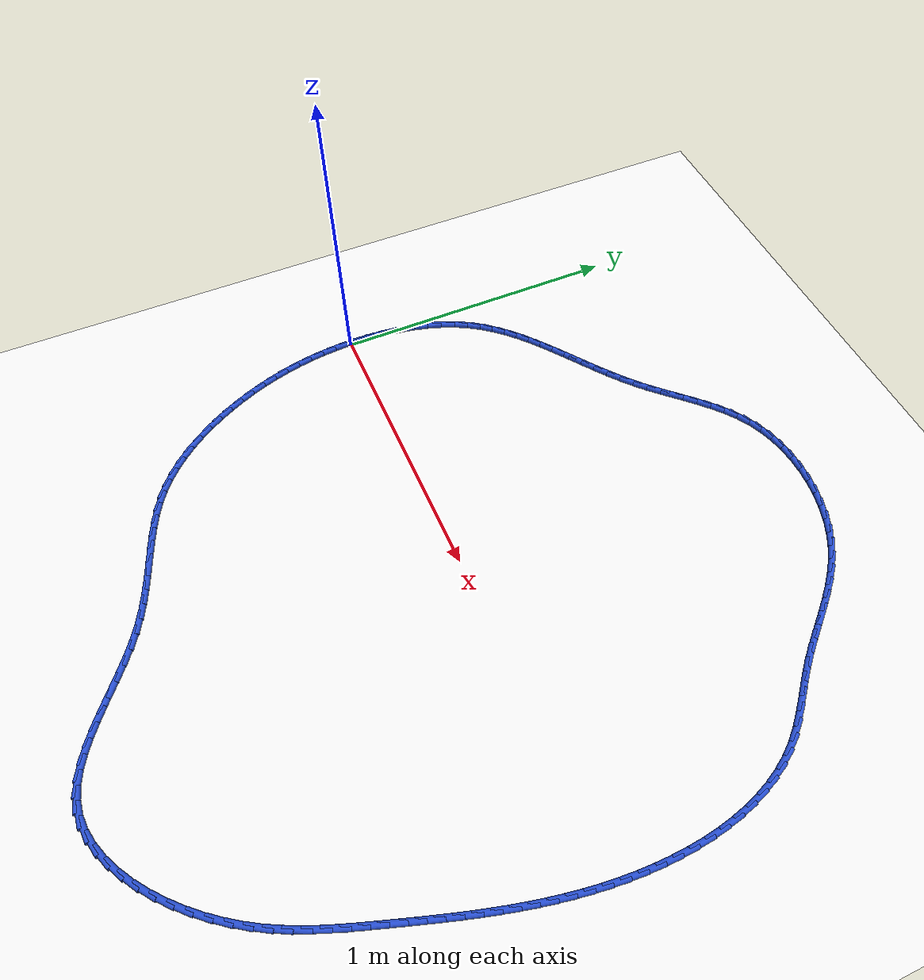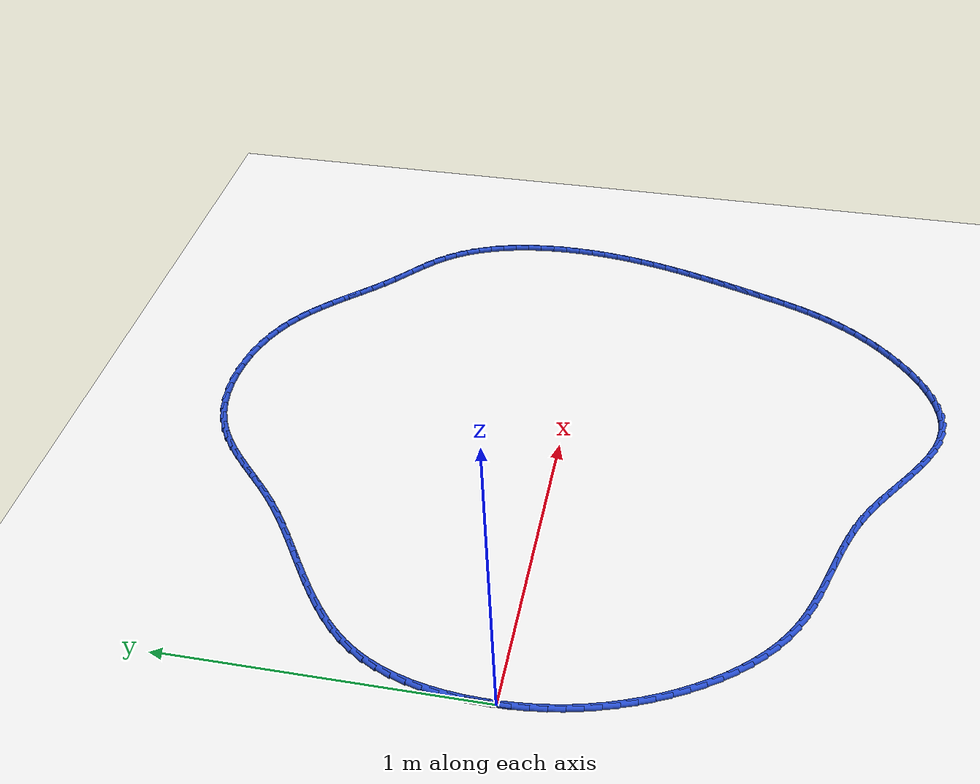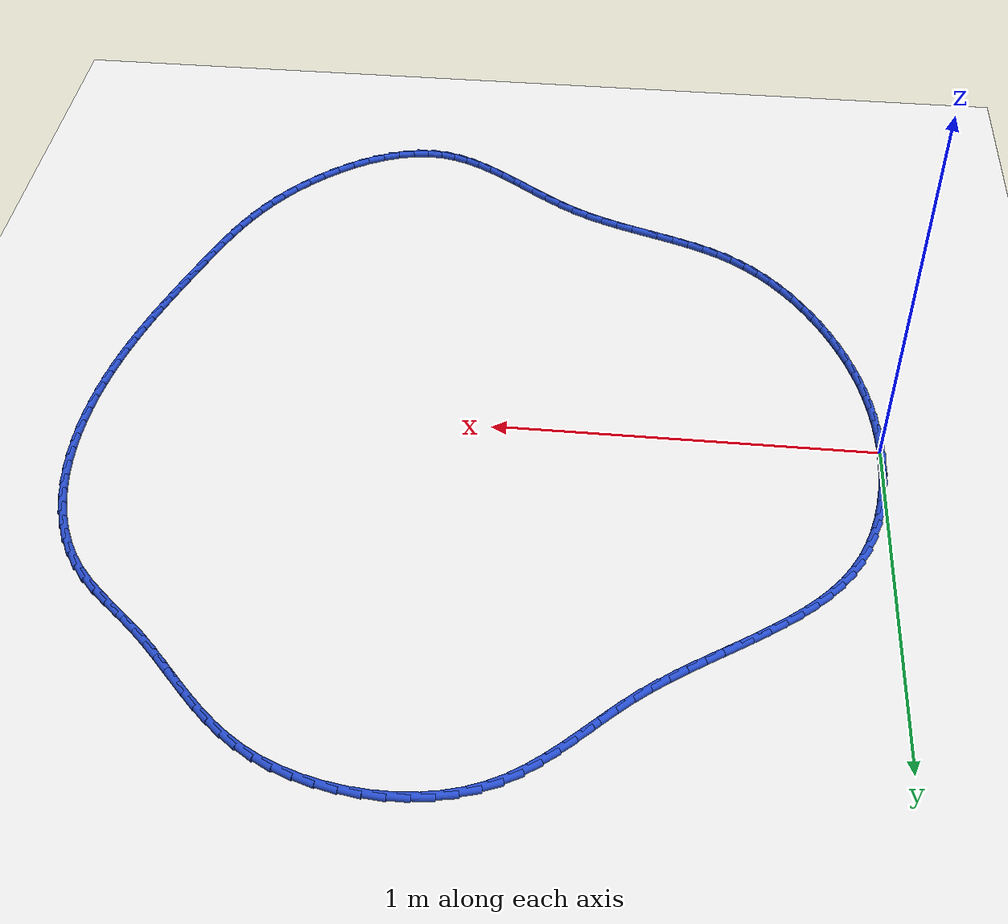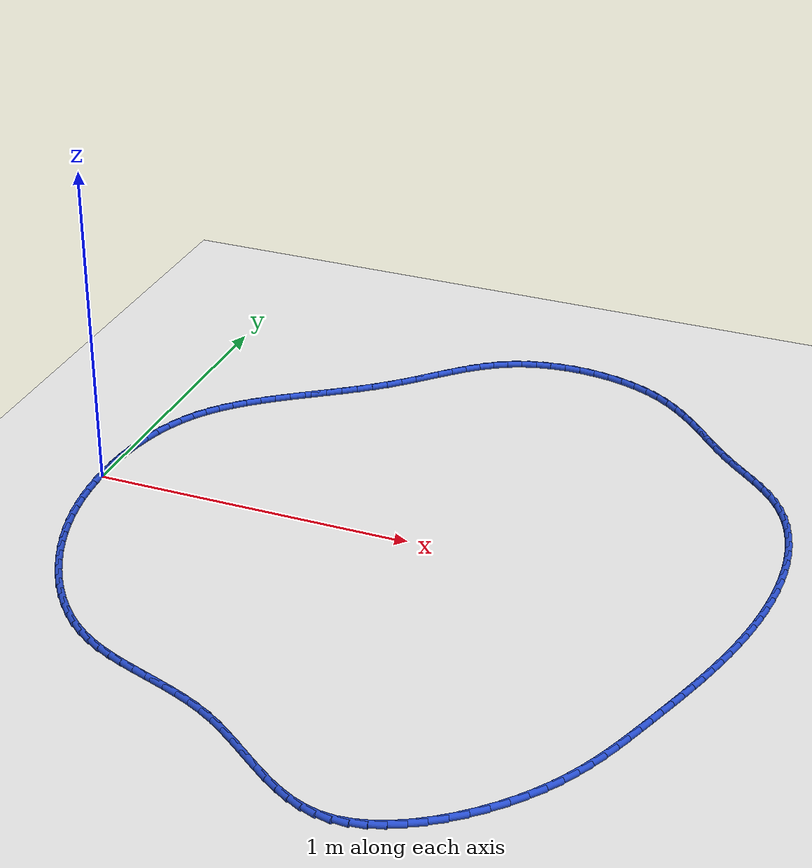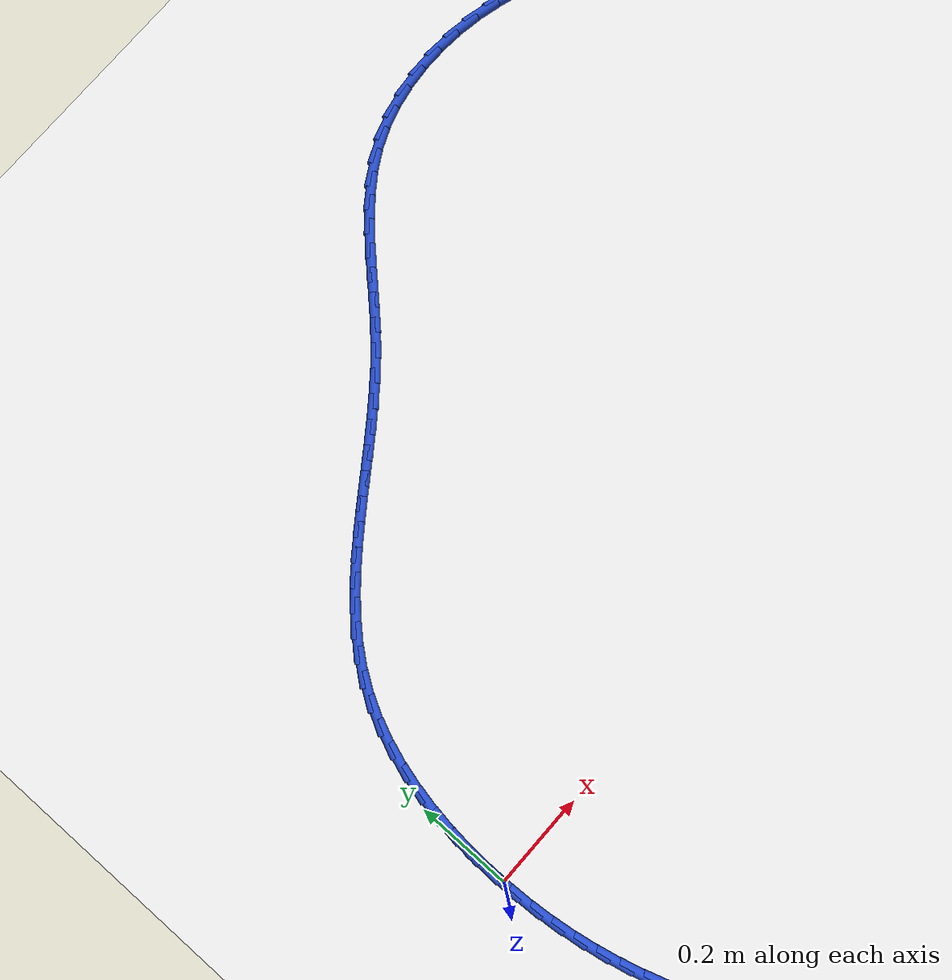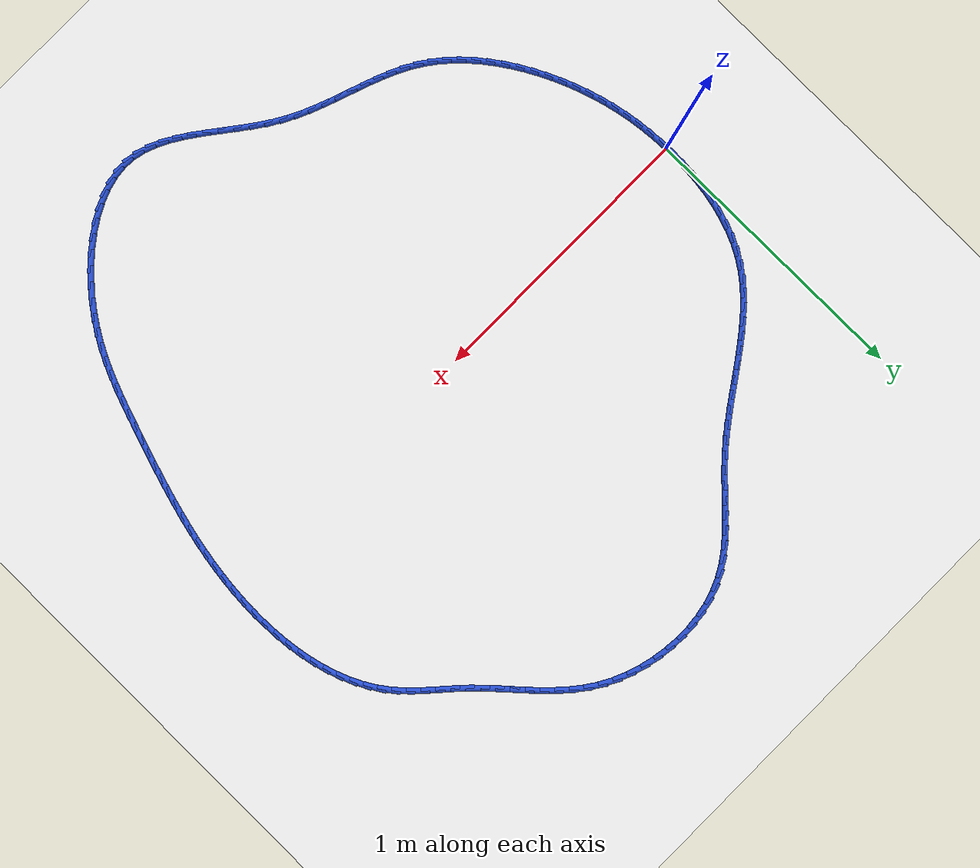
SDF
<sdf version="1.6">
 <world name="default">
  <light name="sun" type="directional">
   <pose>0 0 10 0 -0 0</pose>
   <diffuse>0.8 0.8 0.8 1</diffuse>
   <specular>0.2 0.2 0.2 1</specular>
   <attenuation>
    <range>1000</range>
    <constant>0.9</constant>
    <linear>0.01</linear>
    <quadratic>0.001</quadratic>
   </attenuation>
   <direction>-0.5 0.1 -0.9</direction>
  </light>
  <model name="ground_plane">
   <static>1</static>
   <link name="link">
    <collision name="collision">
     <geometry><plane><normal>0 0 1</normal><size>100 100</size></plane></geometry>
     <surface><friction><ode><mu>100</mu><mu2>50</mu2></ode></friction></surface>
    </collision>
    <visual name="visual">
     <cast_shadows>0</cast_shadows>
     <geometry><plane><normal>0 0 1</normal><size>100 100</size></plane></geometry>
     <material>
      <script><uri>file://media/materials/scripts/gazebo.material</uri><name>Gazebo/WhiteGlow</name></script>
     </material>
    </visual>
   </link>
  </model>
  <gravity>0 0 -9.8</gravity>
  <magnetic_field>6e-06 2.3e-05 -4.2e-05</magnetic_field>
  <atmosphere type="adiabatic"/>
  <physics name="default_physics" default="0" type="ode">
   <max_step_size>0.001</max_step_size>
   <real_time_factor>1</real_time_factor>
   <real_time_update_rate>1000</real_time_update_rate>
  </physics>
  <scene><ambient>0.4 0.4 0.4 1</ambient><background>0.7 0.7 0.7 1</background><shadows>1</shadows></scene>
  <spherical_coordinates>
   <surface_model>EARTH_WGS84</surface_model>
   <latitude_deg>0</latitude_deg>
   <longitude_deg>0</longitude_deg>
   <elevation>0</elevation>
   <heading_deg>0</heading_deg>
  </spherical_coordinates>
  <model name="line">
   <link name="link_0">
    <pose>1.3877787807814457e-17 1.6653345369377348e-16 0.01 0 1.57 1.5703879840936825</pose>
    <collision name="collision">
     <geometry><cylinder><radius>0.01</radius><length>0.08</length></cylinder></geometry>
    </collision>
    <visual name="visual">
     <material>
      <script><name>Gazebo/Blue</name><uri>file://media/materials/scripts/gazebo.material</uri></script>
     </material>
     <geometry><cylinder><radius>0.01</radius><length>0.08</length></cylinder></geometry>
    </visual>
   </link>
   <link name="link_1">
    <pose>2.0461932362918987e-05 0.05010970237685566 0.01 0 1.57 1.5252319487551422</pose>
    <collision name="collision">
     <geometry><cylinder><radius>0.01</radius><length>0.08</length></cylinder></geometry>
    </collision>
    <visual name="visual">
     <material>
      <script><name>Gazebo/Blue</name><uri>file://media/materials/scripts/gazebo.material</uri></script>
     </material>
     <geometry><cylinder><radius>0.01</radius><length>0.08</length></cylinder></geometry>
    </visual>
   </link>
   <link name="link_2">
    <pose>0.002315027762263988 0.10043361292031516 0.01 0 1.57 1.4768614780469314</pose>
    <collision name="collision">
     <geometry><cylinder><radius>0.01</radius><length>0.08</length></cylinder></geometry>
    </collision>
    <visual name="visual">
     <material>
      <script><name>Gazebo/Blue</name><uri>file://media/materials/scripts/gazebo.material</uri></script>
     </material>
     <geometry><cylinder><radius>0.01</radius><length>0.08</length></cylinder></geometry>
    </visual>
   </link>
   <link name="link_3">
    <pose>0.007041752678469361 0.15060470815478336 0.01 0 1.57 1.4244827749581548</pose>
    <collision name="collision">
     <geometry><cylinder><radius>0.01</radius><length>0.08</length></cylinder></geometry>
    </collision>
    <visual name="visual">
     <material>
      <script><name>Gazebo/Blue</name><uri>file://media/materials/scripts/gazebo.material</uri></script>
     </material>
     <geometry><cylinder><radius>0.01</radius><length>0.08</length></cylinder></geometry>
    </visual>
   </link>
   <link name="link_4">
    <pose>0.014358691869745163 0.20025596460466466 0.01 0 1.57 1.3672498876681252</pose>
    <collision name="collision">
     <geometry><cylinder><radius>0.01</radius><length>0.08</length></cylinder></geometry>
    </collision>
    <visual name="visual">
     <material>
      <script><name>Gazebo/Blue</name><uri>file://media/materials/scripts/gazebo.material</uri></script>
     </material>
     <geometry><cylinder><radius>0.01</radius><length>0.08</length></cylinder></geometry>
    </visual>
   </link>
   <link name="link_5">
    <pose>0.02442390052485755 0.2490203587943638 0.01 0 1.57 1.3042676388788637</pose>
    <collision name="collision">
     <geometry><cylinder><radius>0.01</radius><length>0.08</length></cylinder></geometry>
    </collision>
    <visual name="visual">
     <material>
      <script><name>Gazebo/Blue</name><uri>file://media/materials/scripts/gazebo.material</uri></script>
     </material>
     <geometry><cylinder><radius>0.01</radius><length>0.08</length></cylinder></geometry>
    </visual>
   </link>
   <link name="link_6">
    <pose>0.03739543383257267 0.2965308672482853 0.01 0 1.57 1.2346155950224973</pose>
    <collision name="collision">
     <geometry><cylinder><radius>0.01</radius><length>0.08</length></cylinder></geometry>
    </collision>
    <visual name="visual">
     <material>
      <script><name>Gazebo/Blue</name><uri>file://media/materials/scripts/gazebo.material</uri></script>
     </material>
     <geometry><cylinder><radius>0.01</radius><length>0.08</length></cylinder></geometry>
    </visual>
   </link>
   <link name="link_7">
    <pose>0.05343134698165662 0.34242046649083346 0.01 0 1.57 1.1574041959296875</pose>
    <collision name="collision">
     <geometry><cylinder><radius>0.01</radius><length>0.08</length></cylinder></geometry>
    </collision>
    <visual name="visual">
     <material>
      <script><name>Gazebo/Blue</name><uri>file://media/materials/scripts/gazebo.material</uri></script>
     </material>
     <geometry><cylinder><radius>0.01</radius><length>0.08</length></cylinder></geometry>
    </visual>
   </link>
   <link name="link_8">
    <pose>0.0726896951608756 0.3863221330464132 0.01 0 1.57 1.0718764269249268</pose>
    <collision name="collision">
     <geometry><cylinder><radius>0.01</radius><length>0.08</length></cylinder></geometry>
    </collision>
    <visual name="visual">
     <material>
      <script><name>Gazebo/Blue</name><uri>file://media/materials/scripts/gazebo.material</uri></script>
     </material>
     <geometry><cylinder><radius>0.01</radius><length>0.08</length></cylinder></geometry>
    </visual>
   </link>
   <link name="link_9">
    <pose>0.09532853355899572 0.42786884343942905 0.01 0 1.57 0.9794280090093584</pose>
    <collision name="collision">
     <geometry><cylinder><radius>0.01</radius><length>0.08</length></cylinder></geometry>
    </collision>
    <visual name="visual">
     <material>
      <script><name>Gazebo/Blue</name><uri>file://media/materials/scripts/gazebo.material</uri></script>
     </material>
     <geometry><cylinder><radius>0.01</radius><length>0.08</length></cylinder></geometry>
    </visual>
   </link>
   <link name="link_10">
    <pose>0.12144964194261251 0.46676621261109913 0.01 0 1.57 0.8923825192492111</pose>
    <collision name="collision">
     <geometry><cylinder><radius>0.01</radius><length>0.08</length></cylinder></geometry>
    </collision>
    <visual name="visual">
     <material>
      <script><name>Gazebo/Blue</name><uri>file://media/materials/scripts/gazebo.material</uri></script>
     </material>
     <geometry><cylinder><radius>0.01</radius><length>0.08</length></cylinder></geometry>
    </visual>
   </link>
   <link name="link_11">
    <pose>0.15079946091751076 0.5031785153061151 0.01 0 1.57 0.8167372482739383</pose>
    <collision name="collision">
     <geometry><cylinder><radius>0.01</radius><length>0.08</length></cylinder></geometry>
    </collision>
    <visual name="visual">
     <material>
      <script><name>Gazebo/Blue</name><uri>file://media/materials/scripts/gazebo.material</uri></script>
     </material>
     <geometry><cylinder><radius>0.01</radius><length>0.08</length></cylinder></geometry>
    </visual>
   </link>
   <link name="link_12">
    <pose>0.1829861221882732 0.5374485507337933 0.01 0 1.57 0.7532143176928595</pose>
    <collision name="collision">
     <geometry><cylinder><radius>0.01</radius><length>0.08</length></cylinder></geometry>
    </collision>
    <visual name="visual">
     <material>
      <script><name>Gazebo/Blue</name><uri>file://media/materials/scripts/gazebo.material</uri></script>
     </material>
     <geometry><cylinder><radius>0.01</radius><length>0.08</length></cylinder></geometry>
    </visual>
   </link>
   <link name="link_13">
    <pose>0.21761744660018034 0.5699195193501528 0.01 0 1.57 0.7018589598342855</pose>
    <collision name="collision">
     <geometry><cylinder><radius>0.01</radius><length>0.08</length></cylinder></geometry>
    </collision>
    <visual name="visual">
     <material>
      <script><name>Gazebo/Blue</name><uri>file://media/materials/scripts/gazebo.material</uri></script>
     </material>
     <geometry><cylinder><radius>0.01</radius><length>0.08</length></cylinder></geometry>
    </visual>
   </link>
   <link name="link_14">
    <pose>0.2543012549985125 0.6009346216112119 0.01 0 1.57 0.6623294533921383</pose>
    <collision name="collision">
     <geometry><cylinder><radius>0.01</radius><length>0.08</length></cylinder></geometry>
    </collision>
    <visual name="visual">
     <material>
      <script><name>Gazebo/Blue</name><uri>file://media/materials/scripts/gazebo.material</uri></script>
     </material>
     <geometry><cylinder><radius>0.01</radius><length>0.08</length></cylinder></geometry>
    </visual>
   </link>
   <link name="link_15">
    <pose>0.2926453682285506 0.6308370579729903 0.01 0 1.57 0.6341263456896873</pose>
    <collision name="collision">
     <geometry><cylinder><radius>0.01</radius><length>0.08</length></cylinder></geometry>
    </collision>
    <visual name="visual">
     <material>
      <script><name>Gazebo/Blue</name><uri>file://media/materials/scripts/gazebo.material</uri></script>
     </material>
     <geometry><cylinder><radius>0.01</radius><length>0.08</length></cylinder></geometry>
    </visual>
   </link>
   <link name="link_16">
    <pose>0.33225760713557484 0.659970028891506 0.01 0 1.57 0.6167503019242502</pose>
    <collision name="collision">
     <geometry><cylinder><radius>0.01</radius><length>0.08</length></cylinder></geometry>
    </collision>
    <visual name="visual">
     <material>
      <script><name>Gazebo/Blue</name><uri>file://media/materials/scripts/gazebo.material</uri></script>
     </material>
     <geometry><cylinder><radius>0.01</radius><length>0.08</length></cylinder></geometry>
    </visual>
   </link>
   <link name="link_17">
    <pose>0.37274579256486573 0.6886767348227782 0.01 0 1.57 0.6097961670701354</pose>
    <collision name="collision">
     <geometry><cylinder><radius>0.01</radius><length>0.08</length></cylinder></geometry>
    </collision>
    <visual name="visual">
     <material>
      <script><name>Gazebo/Blue</name><uri>file://media/materials/scripts/gazebo.material</uri></script>
     </material>
     <geometry><cylinder><radius>0.01</radius><length>0.08</length></cylinder></geometry>
    </visual>
   </link>
   <link name="link_18">
    <pose>0.4137177453617037 0.7173003762228252 0.01 0 1.57 0.6129990291934921</pose>
    <collision name="collision">
     <geometry><cylinder><radius>0.01</radius><length>0.08</length></cylinder></geometry>
    </collision>
    <visual name="visual">
     <material>
      <script><name>Gazebo/Blue</name><uri>file://media/materials/scripts/gazebo.material</uri></script>
     </material>
     <geometry><cylinder><radius>0.01</radius><length>0.08</length></cylinder></geometry>
    </visual>
   </link>
   <link name="link_19">
    <pose>0.4547812863713694 0.7461841535476663 0.01 0 1.57 0.626245689992034</pose>
    <collision name="collision">
     <geometry><cylinder><radius>0.01</radius><length>0.08</length></cylinder></geometry>
    </collision>
    <visual name="visual">
     <material>
      <script><name>Gazebo/Blue</name><uri>file://media/materials/scripts/gazebo.material</uri></script>
     </material>
     <geometry><cylinder><radius>0.01</radius><length>0.08</length></cylinder></geometry>
    </visual>
   </link>
   <link name="link_20">
    <pose>0.49554423643914336 0.7756712672533201 0.01 0 1.57 0.6495589571418696</pose>
    <collision name="collision">
     <geometry><cylinder><radius>0.01</radius><length>0.08</length></cylinder></geometry>
    </collision>
    <visual name="visual">
     <material>
      <script><name>Gazebo/Blue</name><uri>file://media/materials/scripts/gazebo.material</uri></script>
     </material>
     <geometry><cylinder><radius>0.01</radius><length>0.08</length></cylinder></geometry>
    </visual>
   </link>
   <link name="link_21">
    <pose>0.5356144164103059 0.8061049177958057 0.01 0 1.57 0.6830560161059994</pose>
    <collision name="collision">
     <geometry><cylinder><radius>0.01</radius><length>0.08</length></cylinder></geometry>
    </collision>
    <visual name="visual">
     <material>
      <script><name>Gazebo/Blue</name><uri>file://media/materials/scripts/gazebo.material</uri></script>
     </material>
     <geometry><cylinder><radius>0.01</radius><length>0.08</length></cylinder></geometry>
    </visual>
   </link>
   <link name="link_22">
    <pose>0.5745996471301377 0.8378283056311415 0.01 0 1.57 0.7266561480733533</pose>
    <collision name="collision">
     <geometry><cylinder><radius>0.01</radius><length>0.08</length></cylinder></geometry>
    </collision>
    <visual name="visual">
     <material>
      <script><name>Gazebo/Blue</name><uri>file://media/materials/scripts/gazebo.material</uri></script>
     </material>
     <geometry><cylinder><radius>0.01</radius><length>0.08</length></cylinder></geometry>
    </visual>
   </link>
   <link name="link_23">
    <pose>0.6121148930624188 0.8711761181775799 0.01 0 1.57 0.7689574391367755</pose>
    <collision name="collision">
     <geometry><cylinder><radius>0.01</radius><length>0.08</length></cylinder></geometry>
    </collision>
    <visual name="visual">
     <material>
      <script><name>Gazebo/Blue</name><uri>file://media/materials/scripts/gazebo.material</uri></script>
     </material>
     <geometry><cylinder><radius>0.01</radius><length>0.08</length></cylinder></geometry>
    </visual>
   </link>
   <link name="link_24">
    <pose>0.6481457843085825 0.9060413212563961 0.01 0 1.57 0.7932088401228681</pose>
    <collision name="collision">
     <geometry><cylinder><radius>0.01</radius><length>0.08</length></cylinder></geometry>
    </collision>
    <visual name="visual">
     <material>
      <script><name>Gazebo/Blue</name><uri>file://media/materials/scripts/gazebo.material</uri></script>
     </material>
     <geometry><cylinder><radius>0.01</radius><length>0.08</length></cylinder></geometry>
    </visual>
   </link>
   <link name="link_25">
    <pose>0.6832214286226302 0.9416692193136815 0.01 0 1.57 0.7980828440920179</pose>
    <collision name="collision">
     <geometry><cylinder><radius>0.01</radius><length>0.08</length></cylinder></geometry>
    </collision>
    <visual name="visual">
     <material>
      <script><name>Gazebo/Blue</name><uri>file://media/materials/scripts/gazebo.material</uri></script>
     </material>
     <geometry><cylinder><radius>0.01</radius><length>0.08</length></cylinder></geometry>
    </visual>
   </link>
   <link name="link_26">
    <pose>0.7179142343964778 0.9772535155004892 0.01 0 1.57 0.783272555893107</pose>
    <collision name="collision">
     <geometry><cylinder><radius>0.01</radius><length>0.08</length></cylinder></geometry>
    </collision>
    <visual name="visual">
     <material>
      <script><name>Gazebo/Blue</name><uri>file://media/materials/scripts/gazebo.material</uri></script>
     </material>
     <geometry><cylinder><radius>0.01</radius><length>0.08</length></cylinder></geometry>
    </visual>
   </link>
   <link name="link_27">
    <pose>0.7527966100220406 1.0119879129678722 0.01 0 1.57 0.7480747511756202</pose>
    <collision name="collision">
     <geometry><cylinder><radius>0.01</radius><length>0.08</length></cylinder></geometry>
    </collision>
    <visual name="visual">
     <material>
      <script><name>Gazebo/Blue</name><uri>file://media/materials/scripts/gazebo.material</uri></script>
     </material>
     <geometry><cylinder><radius>0.01</radius><length>0.08</length></cylinder></geometry>
    </visual>
   </link>
   <link name="link_28">
    <pose>0.7884409638912347 1.0450661148668834 0.01 0 1.57 0.6915393473425997</pose>
    <collision name="collision">
     <geometry><cylinder><radius>0.01</radius><length>0.08</length></cylinder></geometry>
    </collision>
    <visual name="visual">
     <material>
      <script><name>Gazebo/Blue</name><uri>file://media/materials/scripts/gazebo.material</uri></script>
     </material>
     <geometry><cylinder><radius>0.01</radius><length>0.08</length></cylinder></geometry>
    </visual>
   </link>
   <link name="link_29">
    <pose>0.8254197043959755 1.075681824348575 0.01 0 1.57 0.6129153265700636</pose>
    <collision name="collision">
     <geometry><cylinder><radius>0.01</radius><length>0.08</length></cylinder></geometry>
    </collision>
    <visual name="visual">
     <material>
      <script><name>Gazebo/Blue</name><uri>file://media/materials/scripts/gazebo.material</uri></script>
     </material>
     <geometry><cylinder><radius>0.01</radius><length>0.08</length></cylinder></geometry>
    </visual>
   </link>
   <link name="link_30">
    <pose>0.8643052399281784 1.1030287445640006 0.01 0 1.57 0.5124660084475797</pose>
    <collision name="collision">
     <geometry><cylinder><radius>0.01</radius><length>0.08</length></cylinder></geometry>
    </collision>
    <visual name="visual">
     <material>
      <script><name>Gazebo/Blue</name><uri>file://media/materials/scripts/gazebo.material</uri></script>
     </material>
     <geometry><cylinder><radius>0.01</radius><length>0.08</length></cylinder></geometry>
    </visual>
   </link>
   <link name="link_31">
    <pose>0.9056699788797593 1.1263005786642126 0.01 0 1.57 0.39546776203038575</pose>
    <collision name="collision">
     <geometry><cylinder><radius>0.01</radius><length>0.08</length></cylinder></geometry>
    </collision>
    <visual name="visual">
     <material>
      <script><name>Gazebo/Blue</name><uri>file://media/materials/scripts/gazebo.material</uri></script>
     </material>
     <geometry><cylinder><radius>0.01</radius><length>0.08</length></cylinder></geometry>
    </visual>
   </link>
   <link name="link_32">
    <pose>0.9499613652537621 1.1447905053636087 0.01 0 1.57 0.2824120084130147</pose>
    <collision name="collision">
     <geometry><cylinder><radius>0.01</radius><length>0.08</length></cylinder></geometry>
    </collision>
    <visual name="visual">
     <material>
      <script><name>Gazebo/Blue</name><uri>file://media/materials/scripts/gazebo.material</uri></script>
     </material>
     <geometry><cylinder><radius>0.01</radius><length>0.08</length></cylinder></geometry>
    </visual>
   </link>
   <link name="link_33">
    <pose>0.9968629138664089 1.1583998149106054 0.01 0 1.57 0.179211980913879</pose>
    <collision name="collision">
     <geometry><cylinder><radius>0.01</radius><length>0.08</length></cylinder></geometry>
    </collision>
    <visual name="visual">
     <material>
      <script><name>Gazebo/Blue</name><uri>file://media/materials/scripts/gazebo.material</uri></script>
     </material>
     <geometry><cylinder><radius>0.01</radius><length>0.08</length></cylinder></geometry>
    </visual>
   </link>
   <link name="link_34">
    <pose>1.045769551238124 1.1672595228662337 0.01 0 1.57 0.08411582880588916</pose>
    <collision name="collision">
     <geometry><cylinder><radius>0.01</radius><length>0.08</length></cylinder></geometry>
    </collision>
    <visual name="visual">
     <material>
      <script><name>Gazebo/Blue</name><uri>file://media/materials/scripts/gazebo.material</uri></script>
     </material>
     <geometry><cylinder><radius>0.01</radius><length>0.08</length></cylinder></geometry>
    </visual>
   </link>
   <link name="link_35">
    <pose>1.0960756673500238 1.1715010718935994 0.01 0 1.57 -0.004797757914438935</pose>
    <collision name="collision">
     <geometry><cylinder><radius>0.01</radius><length>0.08</length></cylinder></geometry>
    </collision>
    <visual name="visual">
     <material>
      <script><name>Gazebo/Blue</name><uri>file://media/materials/scripts/gazebo.material</uri></script>
     </material>
     <geometry><cylinder><radius>0.01</radius><length>0.08</length></cylinder></geometry>
    </visual>
   </link>
   <link name="link_36">
    <pose>1.147175652183225 1.1712559046558095 0.01 0 1.57 -0.08945836000498049</pose>
    <collision name="collision">
     <geometry><cylinder><radius>0.01</radius><length>0.08</length></cylinder></geometry>
    </collision>
    <visual name="visual">
     <material>
      <script><name>Gazebo/Blue</name><uri>file://media/materials/scripts/gazebo.material</uri></script>
     </material>
     <geometry><cylinder><radius>0.01</radius><length>0.08</length></cylinder></geometry>
    </visual>
   </link>
   <link name="link_37">
    <pose>1.1984638957188445 1.1666554638159703 0.01 0 1.57 -0.17175498452302446</pose>
    <collision name="collision">
     <geometry><cylinder><radius>0.01</radius><length>0.08</length></cylinder></geometry>
    </collision>
    <visual name="visual">
     <material>
      <script><name>Gazebo/Blue</name><uri>file://media/materials/scripts/gazebo.material</uri></script>
     </material>
     <geometry><cylinder><radius>0.01</radius><length>0.08</length></cylinder></geometry>
    </visual>
   </link>
   <link name="link_38">
    <pose>1.249334787937998 1.157831192037188 0.01 0 1.57 -0.2535448102509184</pose>
    <collision name="collision">
     <geometry><cylinder><radius>0.01</radius><length>0.08</length></cylinder></geometry>
    </collision>
    <visual name="visual">
     <material>
      <script><name>Gazebo/Blue</name><uri>file://media/materials/scripts/gazebo.material</uri></script>
     </material>
     <geometry><cylinder><radius>0.01</radius><length>0.08</length></cylinder></geometry>
    </visual>
   </link>
   <link name="link_39">
    <pose>1.2991827188218024 1.14491453198257 0.01 0 1.57 -0.336690150724757</pose>
    <collision name="collision">
     <geometry><cylinder><radius>0.01</radius><length>0.08</length></cylinder></geometry>
    </collision>
    <visual name="visual">
     <material>
      <script><name>Gazebo/Blue</name><uri>file://media/materials/scripts/gazebo.material</uri></script>
     </material>
     <geometry><cylinder><radius>0.01</radius><length>0.08</length></cylinder></geometry>
    </visual>
   </link>
   <link name="link_40">
    <pose>1.3474020783513747 1.128036926315222 0.01 0 1.57 -0.42310306907898965</pose>
    <collision name="collision">
     <geometry><cylinder><radius>0.01</radius><length>0.08</length></cylinder></geometry>
    </collision>
    <visual name="visual">
     <material>
      <script><name>Gazebo/Blue</name><uri>file://media/materials/scripts/gazebo.material</uri></script>
     </material>
     <geometry><cylinder><radius>0.01</radius><length>0.08</length></cylinder></geometry>
    </visual>
   </link>
   <link name="link_41">
    <pose>1.3933872565078307 1.107329817698251 0.01 0 1.57 -0.514705143597147</pose>
    <collision name="collision">
     <geometry><cylinder><radius>0.01</radius><length>0.08</length></cylinder></geometry>
    </collision>
    <visual name="visual">
     <material>
      <script><name>Gazebo/Blue</name><uri>file://media/materials/scripts/gazebo.material</uri></script>
     </material>
     <geometry><cylinder><radius>0.01</radius><length>0.08</length></cylinder></geometry>
    </visual>
   </link>
   <link name="link_42">
    <pose>1.4365370466917582 1.0829263519689587 0.01 0 1.57 -0.60643084212509</pose>
    <collision name="collision">
     <geometry><cylinder><radius>0.01</radius><length>0.08</length></cylinder></geometry>
    </collision>
    <visual name="visual">
     <material>
      <script><name>Gazebo/Blue</name><uri>file://media/materials/scripts/gazebo.material</uri></script>
     </material>
     <geometry><cylinder><radius>0.01</radius><length>0.08</length></cylinder></geometry>
    </visual>
   </link>
   <link name="link_43">
    <pose>1.4766397573856311 1.055110333342923 0.01 0 1.57 -0.6852317478385442</pose>
    <collision name="collision">
     <geometry><cylinder><radius>0.01</radius><length>0.08</length></cylinder></geometry>
    </collision>
    <visual name="visual">
     <material>
      <script><name>Gazebo/Blue</name><uri>file://media/materials/scripts/gazebo.material</uri></script>
     </material>
     <geometry><cylinder><radius>0.01</radius><length>0.08</length></cylinder></geometry>
    </visual>
   </link>
   <link name="link_44">
    <pose>1.5141732620211437 1.024432279038108 0.01 0 1.57 -0.7481677094902304</pose>
    <collision name="collision">
     <geometry><cylinder><radius>0.01</radius><length>0.08</length></cylinder></geometry>
    </collision>
    <visual name="visual">
     <material>
      <script><name>Gazebo/Blue</name><uri>file://media/materials/scripts/gazebo.material</uri></script>
     </material>
     <geometry><cylinder><radius>0.01</radius><length>0.08</length></cylinder></geometry>
    </visual>
   </link>
   <link name="link_45">
    <pose>1.549686055335538 0.9914700214955859 0.01 0 1.57 -0.7945386288861598</pose>
    <collision name="collision">
     <geometry><cylinder><radius>0.01</radius><length>0.08</length></cylinder></geometry>
    </collision>
    <visual name="visual">
     <material>
      <script><name>Gazebo/Blue</name><uri>file://media/materials/scripts/gazebo.material</uri></script>
     </material>
     <geometry><cylinder><radius>0.01</radius><length>0.08</length></cylinder></geometry>
    </visual>
   </link>
   <link name="link_46">
    <pose>1.5837266320660597 0.9568013931564292 0.01 0 1.57 -0.824272132206903</pose>
    <collision name="collision">
     <geometry><cylinder><radius>0.01</radius><length>0.08</length></cylinder></geometry>
    </collision>
    <visual name="visual">
     <material>
      <script><name>Gazebo/Blue</name><uri>file://media/materials/scripts/gazebo.material</uri></script>
     </material>
     <geometry><cylinder><radius>0.01</radius><length>0.08</length></cylinder></geometry>
    </visual>
   </link>
   <link name="link_47">
    <pose>1.6168434869499513 0.9210042264617111 0.01 0 1.57 -0.8375475506481883</pose>
    <collision name="collision">
     <geometry><cylinder><radius>0.01</radius><length>0.08</length></cylinder></geometry>
    </collision>
    <visual name="visual">
     <material>
      <script><name>Gazebo/Blue</name><uri>file://media/materials/scripts/gazebo.material</uri></script>
     </material>
     <geometry><cylinder><radius>0.01</radius><length>0.08</length></cylinder></geometry>
    </visual>
   </link>
   <link name="link_48">
    <pose>1.649585114724456 0.8846563538525027 0.01 0 1.57 -0.834550700331224</pose>
    <collision name="collision">
     <geometry><cylinder><radius>0.01</radius><length>0.08</length></cylinder></geometry>
    </collision>
    <visual name="visual">
     <material>
      <script><name>Gazebo/Blue</name><uri>file://media/materials/scripts/gazebo.material</uri></script>
     </material>
     <geometry><cylinder><radius>0.01</radius><length>0.08</length></cylinder></geometry>
    </visual>
   </link>
   <link name="link_49">
    <pose>1.6825000101268188 0.8483356077698782 0.01 0 1.57 -0.8153683657946804</pose>
    <collision name="collision">
     <geometry><cylinder><radius>0.01</radius><length>0.08</length></cylinder></geometry>
    </collision>
    <visual name="visual">
     <material>
      <script><name>Gazebo/Blue</name><uri>file://media/materials/scripts/gazebo.material</uri></script>
     </material>
     <geometry><cylinder><radius>0.01</radius><length>0.08</length></cylinder></geometry>
    </visual>
   </link>
   <link name="link_50">
    <pose>1.716136667894282 0.8126198206549083 0.01 0 1.57 -0.7800877470952488</pose>
    <collision name="collision">
     <geometry><cylinder><radius>0.01</radius><length>0.08</length></cylinder></geometry>
    </collision>
    <visual name="visual">
     <material>
      <script><name>Gazebo/Blue</name><uri>file://media/materials/scripts/gazebo.material</uri></script>
     </material>
     <geometry><cylinder><radius>0.01</radius><length>0.08</length></cylinder></geometry>
    </visual>
   </link>
   <link name="link_51">
    <pose>1.7510408597299338 0.7780843856122343 0.01 0 1.57 -0.7417299932349543</pose>
    <collision name="collision">
     <geometry><cylinder><radius>0.01</radius><length>0.08</length></cylinder></geometry>
    </collision>
    <visual name="visual">
     <material>
      <script><name>Gazebo/Blue</name><uri>file://media/materials/scripts/gazebo.material</uri></script>
     </material>
     <geometry><cylinder><radius>0.01</radius><length>0.08</length></cylinder></geometry>
    </visual>
   </link>
   <link name="link_52">
    <pose>1.7872819232547235 0.7448778986710395 0.01 0 1.57 -0.7278646358349814</pose>
    <collision name="collision">
     <geometry><cylinder><radius>0.01</radius><length>0.08</length></cylinder></geometry>
    </collision>
    <visual name="visual">
     <material>
      <script><name>Gazebo/Blue</name><uri>file://media/materials/scripts/gazebo.material</uri></script>
     </material>
     <geometry><cylinder><radius>0.01</radius><length>0.08</length></cylinder></geometry>
    </visual>
   </link>
   <link name="link_53">
    <pose>1.8239119209292864 0.7122376649188343 0.01 0 1.57 -0.742079083661313</pose>
    <collision name="collision">
     <geometry><cylinder><radius>0.01</radius><length>0.08</length></cylinder></geometry>
    </collision>
    <visual name="visual">
     <material>
      <script><name>Gazebo/Blue</name><uri>file://media/materials/scripts/gazebo.material</uri></script>
     </material>
     <geometry><cylinder><radius>0.01</radius><length>0.08</length></cylinder></geometry>
    </visual>
   </link>
   <link name="link_54">
    <pose>1.8598520880321094 0.6792837924145709 0.01 0 1.57 -0.7850444020713876</pose>
    <collision name="collision">
     <geometry><cylinder><radius>0.01</radius><length>0.08</length></cylinder></geometry>
    </collision>
    <visual name="visual">
     <material>
      <script><name>Gazebo/Blue</name><uri>file://media/materials/scripts/gazebo.material</uri></script>
     </material>
     <geometry><cylinder><radius>0.01</radius><length>0.08</length></cylinder></geometry>
    </visual>
   </link>
   <link name="link_55">
    <pose>1.8940236598416815 0.6451363892172006 0.01 0 1.57 -0.857748095594117</pose>
    <collision name="collision">
     <geometry><cylinder><radius>0.01</radius><length>0.08</length></cylinder></geometry>
    </collision>
    <visual name="visual">
     <material>
      <script><name>Gazebo/Blue</name><uri>file://media/materials/scripts/gazebo.material</uri></script>
     </material>
     <geometry><cylinder><radius>0.01</radius><length>0.08</length></cylinder></geometry>
    </visual>
   </link>
   <link name="link_56">
    <pose>1.9253484853503648 0.6089161372248094 0.01 0 1.57 -0.9516864187576456</pose>
    <collision name="collision">
     <geometry><cylinder><radius>0.01</radius><length>0.08</length></cylinder></geometry>
    </collision>
    <visual name="visual">
     <material>
      <script><name>Gazebo/Blue</name><uri>file://media/materials/scripts/gazebo.material</uri></script>
     </material>
     <geometry><cylinder><radius>0.01</radius><length>0.08</length></cylinder></geometry>
    </visual>
   </link>
   <link name="link_57">
    <pose>1.9530562932289688 0.5700315941927345 0.01 0 1.57 -1.0429962687888408</pose>
    <collision name="collision">
     <geometry><cylinder><radius>0.01</radius><length>0.08</length></cylinder></geometry>
    </collision>
    <visual name="visual">
     <material>
      <script><name>Gazebo/Blue</name><uri>file://media/materials/scripts/gazebo.material</uri></script>
     </material>
     <geometry><cylinder><radius>0.01</radius><length>0.08</length></cylinder></geometry>
    </visual>
   </link>
   <link name="link_58">
    <pose>1.9771831179195656 0.5286452356609538 0.01 0 1.57 -1.1273394929139826</pose>
    <collision name="collision">
     <geometry><cylinder><radius>0.01</radius><length>0.08</length></cylinder></geometry>
    </collision>
    <visual name="visual">
     <material>
      <script><name>Gazebo/Blue</name><uri>file://media/materials/scripts/gazebo.material</uri></script>
     </material>
     <geometry><cylinder><radius>0.01</radius><length>0.08</length></cylinder></geometry>
    </visual>
   </link>
   <link name="link_59">
    <pose>1.9978953726609967 0.4850414448837725 0.01 0 1.57 -1.204580721750172</pose>
    <collision name="collision">
     <geometry><cylinder><radius>0.01</radius><length>0.08</length></cylinder></geometry>
    </collision>
    <visual name="visual">
     <material>
      <script><name>Gazebo/Blue</name><uri>file://media/materials/scripts/gazebo.material</uri></script>
     </material>
     <geometry><cylinder><radius>0.01</radius><length>0.08</length></cylinder></geometry>
    </visual>
   </link>
   <link name="link_60">
    <pose>2.015359470692105 0.43950460511549716 0.01 0 1.57 -1.2749375806439829</pose>
    <collision name="collision">
     <geometry><cylinder><radius>0.01</radius><length>0.08</length></cylinder></geometry>
    </collision>
    <visual name="visual">
     <material>
      <script><name>Gazebo/Blue</name><uri>file://media/materials/scripts/gazebo.material</uri></script>
     </material>
     <geometry><cylinder><radius>0.01</radius><length>0.08</length></cylinder></geometry>
    </visual>
   </link>
   <link name="link_61">
    <pose>2.02974182525173 0.392319099610433 0.01 0 1.57 -1.3388559705312604</pose>
    <collision name="collision">
     <geometry><cylinder><radius>0.01</radius><length>0.08</length></cylinder></geometry>
    </collision>
    <visual name="visual">
     <material>
      <script><name>Gazebo/Blue</name><uri>file://media/materials/scripts/gazebo.material</uri></script>
     </material>
     <geometry><cylinder><radius>0.01</radius><length>0.08</length></cylinder></geometry>
    </visual>
   </link>
   <link name="link_62">
    <pose>2.041208849578717 0.3437693116228865 0.01 0 1.57 -1.3969072855628595</pose>
    <collision name="collision">
     <geometry><cylinder><radius>0.01</radius><length>0.08</length></cylinder></geometry>
    </collision>
    <visual name="visual">
     <material>
      <script><name>Gazebo/Blue</name><uri>file://media/materials/scripts/gazebo.material</uri></script>
     </material>
     <geometry><cylinder><radius>0.01</radius><length>0.08</length></cylinder></geometry>
    </visual>
   </link>
   <link name="link_63">
    <pose>2.0499269569119045 0.29413962440716285 0.01 0 1.57 -1.4497142209687925</pose>
    <collision name="collision">
     <geometry><cylinder><radius>0.01</radius><length>0.08</length></cylinder></geometry>
    </collision>
    <visual name="visual">
     <material>
      <script><name>Gazebo/Blue</name><uri>file://media/materials/scripts/gazebo.material</uri></script>
     </material>
     <geometry><cylinder><radius>0.01</radius><length>0.08</length></cylinder></geometry>
    </visual>
   </link>
   <link name="link_64">
    <pose>2.0560625604901364 0.2437144212175688 0.01 0 1.57 -1.4979029227534368</pose>
    <collision name="collision">
     <geometry><cylinder><radius>0.01</radius><length>0.08</length></cylinder></geometry>
    </collision>
    <visual name="visual">
     <material>
      <script><name>Gazebo/Blue</name><uri>file://media/materials/scripts/gazebo.material</uri></script>
     </material>
     <geometry><cylinder><radius>0.01</radius><length>0.08</length></cylinder></geometry>
    </visual>
   </link>
   <link name="link_65">
    <pose>2.059782073552254 0.19277808530840967 0.01 0 1.57 -1.5420757832447567</pose>
    <collision name="collision">
     <geometry><cylinder><radius>0.01</radius><length>0.08</length></cylinder></geometry>
    </collision>
    <visual name="visual">
     <material>
      <script><name>Gazebo/Blue</name><uri>file://media/materials/scripts/gazebo.material</uri></script>
     </material>
     <geometry><cylinder><radius>0.01</radius><length>0.08</length></cylinder></geometry>
    </visual>
   </link>
   <link name="link_66">
    <pose>2.061251909337098 0.14161499993399096 0.01 0 1.57 1.5587937169576045</pose>
    <collision name="collision">
     <geometry><cylinder><radius>0.01</radius><length>0.08</length></cylinder></geometry>
    </collision>
    <visual name="visual">
     <material>
      <script><name>Gazebo/Blue</name><uri>file://media/materials/scripts/gazebo.material</uri></script>
     </material>
     <geometry><cylinder><radius>0.01</radius><length>0.08</length></cylinder></geometry>
    </visual>
   </link>
   <link name="link_67">
    <pose>2.060638481083512 0.09050954834861945 0.01 0 1.57 1.5209930240548928</pose>
    <collision name="collision">
     <geometry><cylinder><radius>0.01</radius><length>0.08</length></cylinder></geometry>
    </collision>
    <visual name="visual">
     <material>
      <script><name>Gazebo/Blue</name><uri>file://media/materials/scripts/gazebo.material</uri></script>
     </material>
     <geometry><cylinder><radius>0.01</radius><length>0.08</length></cylinder></geometry>
    </visual>
   </link>
   <link name="link_68">
    <pose>2.058108202030337 0.039746113806600036 0.01 0 1.57 1.4855934213183464</pose>
    <collision name="collision">
     <geometry><cylinder><radius>0.01</radius><length>0.08</length></cylinder></geometry>
    </collision>
    <visual name="visual">
     <material>
      <script><name>Gazebo/Blue</name><uri>file://media/materials/scripts/gazebo.material</uri></script>
     </material>
     <geometry><cylinder><radius>0.01</radius><length>0.08</length></cylinder></geometry>
    </visual>
   </link>
   <link name="link_69">
    <pose>2.0538221448049563 -0.010436219579469096 0.01 0 1.57 1.4522254163975166</pose>
    <collision name="collision">
     <geometry><cylinder><radius>0.01</radius><length>0.08</length></cylinder></geometry>
    </collision>
    <visual name="visual">
     <material>
      <script><name>Gazebo/Blue</name><uri>file://media/materials/scripts/gazebo.material</uri></script>
     </material>
     <geometry><cylinder><radius>0.01</radius><length>0.08</length></cylinder></geometry>
    </visual>
   </link>
   <link name="link_70">
    <pose>2.047916145970382 -0.060012420350824346 0.01 0 1.57 1.4209821458318201</pose>
    <collision name="collision">
     <geometry><cylinder><radius>0.01</radius><length>0.08</length></cylinder></geometry>
    </collision>
    <visual name="visual">
     <material>
      <script><name>Gazebo/Blue</name><uri>file://media/materials/scripts/gazebo.material</uri></script>
     </material>
     <geometry><cylinder><radius>0.01</radius><length>0.08</length></cylinder></geometry>
    </visual>
   </link>
   <link name="link_71">
    <pose>2.0405185952522613 -0.1090206212282597 0.01 0 1.57 1.39201190825248</pose>
    <collision name="collision">
     <geometry><cylinder><radius>0.01</radius><length>0.08</length></cylinder></geometry>
    </collision>
    <visual name="visual">
     <material>
      <script><name>Gazebo/Blue</name><uri>file://media/materials/scripts/gazebo.material</uri></script>
     </material>
     <geometry><cylinder><radius>0.01</radius><length>0.08</length></cylinder></geometry>
    </visual>
   </link>
   <link name="link_72">
    <pose>2.0317578812958765 -0.15749896409623826 0.01 0 1.57 1.3654353971454807</pose>
    <collision name="collision">
     <geometry><cylinder><radius>0.01</radius><length>0.08</length></cylinder></geometry>
    </collision>
    <visual name="visual">
     <material>
      <script><name>Gazebo/Blue</name><uri>file://media/materials/scripts/gazebo.material</uri></script>
     </material>
     <geometry><cylinder><radius>0.01</radius><length>0.08</length></cylinder></geometry>
    </visual>
   </link>
   <link name="link_73">
    <pose>2.0217623927465103 -0.2054855908392234 0.01 0 1.57 1.3413483488446771</pose>
    <collision name="collision">
     <geometry><cylinder><radius>0.01</radius><length>0.08</length></cylinder></geometry>
    </collision>
    <visual name="visual">
     <material>
      <script><name>Gazebo/Blue</name><uri>file://media/materials/scripts/gazebo.material</uri></script>
     </material>
     <geometry><cylinder><radius>0.01</radius><length>0.08</length></cylinder></geometry>
    </visual>
   </link>
   <link name="link_74">
    <pose>2.010660518249443 -0.2530186433416763 0.01 0 1.57 1.3198248910323733</pose>
    <collision name="collision">
     <geometry><cylinder><radius>0.01</radius><length>0.08</length></cylinder></geometry>
    </collision>
    <visual name="visual">
     <material>
      <script><name>Gazebo/Blue</name><uri>file://media/materials/scripts/gazebo.material</uri></script>
     </material>
     <geometry><cylinder><radius>0.01</radius><length>0.08</length></cylinder></geometry>
    </visual>
   </link>
   <link name="link_75">
    <pose>1.9985806464499571 -0.3001362634880604 0.01 0 1.57 1.3009212516885558</pose>
    <collision name="collision">
     <geometry><cylinder><radius>0.01</radius><length>0.08</length></cylinder></geometry>
    </collision>
    <visual name="visual">
     <material>
      <script><name>Gazebo/Blue</name><uri>file://media/materials/scripts/gazebo.material</uri></script>
     </material>
     <geometry><cylinder><radius>0.01</radius><length>0.08</length></cylinder></geometry>
    </visual>
   </link>
   <link name="link_76">
    <pose>1.9856511659933358 -0.3468765931628384 0.01 0 1.57 1.284679543516372</pose>
    <collision name="collision">
     <geometry><cylinder><radius>0.01</radius><length>0.08</length></cylinder></geometry>
    </collision>
    <visual name="visual">
     <material>
      <script><name>Gazebo/Blue</name><uri>file://media/materials/scripts/gazebo.material</uri></script>
     </material>
     <geometry><cylinder><radius>0.01</radius><length>0.08</length></cylinder></geometry>
    </visual>
   </link>
   <link name="link_77">
    <pose>1.9720004655248597 -0.393277774250473 0.01 0 1.57 1.2711313987236612</pose>
    <collision name="collision">
     <geometry><cylinder><radius>0.01</radius><length>0.08</length></cylinder></geometry>
    </collision>
    <visual name="visual">
     <material>
      <script><name>Gazebo/Blue</name><uri>file://media/materials/scripts/gazebo.material</uri></script>
     </material>
     <geometry><cylinder><radius>0.01</radius><length>0.08</length></cylinder></geometry>
    </visual>
   </link>
   <link name="link_78">
    <pose>1.957756933689811 -0.43937794863542773 0.01 0 1.57 1.2603012883070623</pose>
    <collision name="collision">
     <geometry><cylinder><radius>0.01</radius><length>0.08</length></cylinder></geometry>
    </collision>
    <visual name="visual">
     <material>
      <script><name>Gazebo/Blue</name><uri>file://media/materials/scripts/gazebo.material</uri></script>
     </material>
     <geometry><cylinder><radius>0.01</radius><length>0.08</length></cylinder></geometry>
    </visual>
   </link>
   <link name="link_79">
    <pose>1.943048959133472 -0.4852152582021636 0.01 0 1.57 1.2522094112883007</pose>
    <collision name="collision">
     <geometry><cylinder><radius>0.01</radius><length>0.08</length></cylinder></geometry>
    </collision>
    <visual name="visual">
     <material>
      <script><name>Gazebo/Blue</name><uri>file://media/materials/scripts/gazebo.material</uri></script>
     </material>
     <geometry><cylinder><radius>0.01</radius><length>0.08</length></cylinder></geometry>
    </visual>
   </link>
   <link name="link_80">
    <pose>1.9280049305011242 -0.530827844835144 0.01 0 1.57 1.24687407889715</pose>
    <collision name="collision">
     <geometry><cylinder><radius>0.01</radius><length>0.08</length></cylinder></geometry>
    </collision>
    <visual name="visual">
     <material>
      <script><name>Gazebo/Blue</name><uri>file://media/materials/scripts/gazebo.material</uri></script>
     </material>
     <geometry><cylinder><radius>0.01</radius><length>0.08</length></cylinder></geometry>
    </visual>
   </link>
   <link name="link_81">
    <pose>1.9127532364380497 -0.5762538504188318 0.01 0 1.57 1.2441341679801499</pose>
    <collision name="collision">
     <geometry><cylinder><radius>0.01</radius><length>0.08</length></cylinder></geometry>
    </collision>
    <visual name="visual">
     <material>
      <script><name>Gazebo/Blue</name><uri>file://media/materials/scripts/gazebo.material</uri></script>
     </material>
     <geometry><cylinder><radius>0.01</radius><length>0.08</length></cylinder></geometry>
    </visual>
   </link>
   <link name="link_82">
    <pose>1.897413605455581 -0.6215302558179849 0.01 0 1.57 1.2385742932887691</pose>
    <collision name="collision">
     <geometry><cylinder><radius>0.01</radius><length>0.08</length></cylinder></geometry>
    </collision>
    <visual name="visual">
     <material>
      <script><name>Gazebo/Blue</name><uri>file://media/materials/scripts/gazebo.material</uri></script>
     </material>
     <geometry><cylinder><radius>0.01</radius><length>0.08</length></cylinder></geometry>
    </visual>
   </link>
   <link name="link_83">
    <pose>1.881843787986128 -0.6666589198410778 0.01 0 1.57 1.2239502533319593</pose>
    <collision name="collision">
     <geometry><cylinder><radius>0.01</radius><length>0.08</length></cylinder></geometry>
    </collision>
    <visual name="visual">
     <material>
      <script><name>Gazebo/Blue</name><uri>file://media/materials/scripts/gazebo.material</uri></script>
     </material>
     <geometry><cylinder><radius>0.01</radius><length>0.08</length></cylinder></geometry>
    </visual>
   </link>
   <link name="link_84">
    <pose>1.8655990413877728 -0.711601147602838 0.01 0 1.57 1.200057954285988</pose>
    <collision name="collision">
     <geometry><cylinder><radius>0.01</radius><length>0.08</length></cylinder></geometry>
    </collision>
    <visual name="visual">
     <material>
      <script><name>Gazebo/Blue</name><uri>file://media/materials/scripts/gazebo.material</uri></script>
     </material>
     <geometry><cylinder><radius>0.01</radius><length>0.08</length></cylinder></geometry>
    </visual>
   </link>
   <link name="link_85">
    <pose>1.848217807325559 -0.7563159898243439 0.01 0 1.57 1.1672210607373954</pose>
    <collision name="collision">
     <geometry><cylinder><radius>0.01</radius><length>0.08</length></cylinder></geometry>
    </collision>
    <visual name="visual">
     <material>
      <script><name>Gazebo/Blue</name><uri>file://media/materials/scripts/gazebo.material</uri></script>
     </material>
     <geometry><cylinder><radius>0.01</radius><length>0.08</length></cylinder></geometry>
    </visual>
   </link>
   <link name="link_86">
    <pose>1.8292385274645269 -0.8007624972266731 0.01 0 1.57 1.1259864175706435</pose>
    <collision name="collision">
     <geometry><cylinder><radius>0.01</radius><length>0.08</length></cylinder></geometry>
    </collision>
    <visual name="visual">
     <material>
      <script><name>Gazebo/Blue</name><uri>file://media/materials/scripts/gazebo.material</uri></script>
     </material>
     <geometry><cylinder><radius>0.01</radius><length>0.08</length></cylinder></geometry>
    </visual>
   </link>
   <link name="link_87">
    <pose>1.8081996434697185 -0.8448997205309043 0.01 0 1.57 1.077165963917169</pose>
    <collision name="collision">
     <geometry><cylinder><radius>0.01</radius><length>0.08</length></cylinder></geometry>
    </collision>
    <visual name="visual">
     <material>
      <script><name>Gazebo/Blue</name><uri>file://media/materials/scripts/gazebo.material</uri></script>
     </material>
     <geometry><cylinder><radius>0.01</radius><length>0.08</length></cylinder></geometry>
    </visual>
   </link>
   <link name="link_88">
    <pose>1.7846395970061766 -0.888686710458114 0.01 0 1.57 1.021859325094769</pose>
    <collision name="collision">
     <geometry><cylinder><radius>0.01</radius><length>0.08</length></cylinder></geometry>
    </collision>
    <visual name="visual">
     <material>
      <script><name>Gazebo/Blue</name><uri>file://media/materials/scripts/gazebo.material</uri></script>
     </material>
     <geometry><cylinder><radius>0.01</radius><length>0.08</length></cylinder></geometry>
    </visual>
   </link>
   <link name="link_89">
    <pose>1.758096829738943 -0.9320825177293809 0.01 0 1.57 0.9619548756649698</pose>
    <collision name="collision">
     <geometry><cylinder><radius>0.01</radius><length>0.08</length></cylinder></geometry>
    </collision>
    <visual name="visual">
     <material>
      <script><name>Gazebo/Blue</name><uri>file://media/materials/scripts/gazebo.material</uri></script>
     </material>
     <geometry><cylinder><radius>0.01</radius><length>0.08</length></cylinder></geometry>
    </visual>
   </link>
   <link name="link_90">
    <pose>1.7281741307879246 -0.9750011643839988 0.01 0 1.57 0.9021735652837843</pose>
    <collision name="collision">
     <geometry><cylinder><radius>0.01</radius><length>0.08</length></cylinder></geometry>
    </collision>
    <visual name="visual">
     <material>
      <script><name>Gazebo/Blue</name><uri>file://media/materials/scripts/gazebo.material</uri></script>
     </material>
     <geometry><cylinder><radius>0.01</radius><length>0.08</length></cylinder></geometry>
    </visual>
   </link>
   <link name="link_91">
    <pose>1.6950073276309856 -1.0169836660284508 0.01 0 1.57 0.8428026870314624</pose>
    <collision name="collision">
     <geometry><cylinder><radius>0.01</radius><length>0.08</length></cylinder></geometry>
    </collision>
    <visual name="visual">
     <material>
      <script><name>Gazebo/Blue</name><uri>file://media/materials/scripts/gazebo.material</uri></script>
     </material>
     <geometry><cylinder><radius>0.01</radius><length>0.08</length></cylinder></geometry>
    </visual>
   </link>
   <link name="link_92">
    <pose>1.6589956579777332 -1.057386710613545 0.01 0 1.57 0.7817906324800181</pose>
    <collision name="collision">
     <geometry><cylinder><radius>0.01</radius><length>0.08</length></cylinder></geometry>
    </collision>
    <visual name="visual">
     <material>
      <script><name>Gazebo/Blue</name><uri>file://media/materials/scripts/gazebo.material</uri></script>
     </material>
     <geometry><cylinder><radius>0.01</radius><length>0.08</length></cylinder></geometry>
    </visual>
   </link>
   <link name="link_93">
    <pose>1.6205402274674232 -1.0955656789613162 0.01 0 1.57 0.7170714353190663</pose>
    <collision name="collision">
     <geometry><cylinder><radius>0.01</radius><length>0.08</length></cylinder></geometry>
    </collision>
    <visual name="visual">
     <material>
      <script><name>Gazebo/Blue</name><uri>file://media/materials/scripts/gazebo.material</uri></script>
     </material>
     <geometry><cylinder><radius>0.01</radius><length>0.08</length></cylinder></geometry>
    </visual>
   </link>
   <link name="link_94">
    <pose>1.5800421417393125 -1.1308759518937983 0.01 0 1.57 0.6464142626570827</pose>
    <collision name="collision">
     <geometry><cylinder><radius>0.01</radius><length>0.08</length></cylinder></geometry>
    </collision>
    <visual name="visual">
     <material>
      <script><name>Gazebo/Blue</name><uri>file://media/materials/scripts/gazebo.material</uri></script>
     </material>
     <geometry><cylinder><radius>0.01</radius><length>0.08</length></cylinder></geometry>
    </visual>
   </link>
   <link name="link_95">
    <pose>1.537902506432656 -1.1626729102330255 0.01 0 1.57 0.5672790024577486</pose>
    <collision name="collision">
     <geometry><cylinder><radius>0.01</radius><length>0.08</length></cylinder></geometry>
    </collision>
    <visual name="visual">
     <material>
      <script><name>Gazebo/Blue</name><uri>file://media/materials/scripts/gazebo.material</uri></script>
     </material>
     <geometry><cylinder><radius>0.01</radius><length>0.08</length></cylinder></geometry>
    </visual>
   </link>
   <link name="link_96">
    <pose>1.4945224271867117 -1.1903119348010314 0.01 0 1.57 0.4767092942284722</pose>
    <collision name="collision">
     <geometry><cylinder><radius>0.01</radius><length>0.08</length></cylinder></geometry>
    </collision>
    <visual name="visual">
     <material>
      <script><name>Gazebo/Blue</name><uri>file://media/materials/scripts/gazebo.material</uri></script>
     </material>
     <geometry><cylinder><radius>0.01</radius><length>0.08</length></cylinder></geometry>
    </visual>
   </link>
   <link name="link_97">
    <pose>1.4503030096407363 -1.21314840641985 0.01 0 1.57 0.3713276064531596</pose>
    <collision name="collision">
     <geometry><cylinder><radius>0.01</radius><length>0.08</length></cylinder></geometry>
    </collision>
    <visual name="visual">
     <material>
      <script><name>Gazebo/Blue</name><uri>file://media/materials/scripts/gazebo.material</uri></script>
     </material>
     <geometry><cylinder><radius>0.01</radius><length>0.08</length></cylinder></geometry>
    </visual>
   </link>
   <link name="link_98">
    <pose>1.4056453594339857 -1.2305377059115155 0.01 0 1.57 0.24758421453411017</pose>
    <collision name="collision">
     <geometry><cylinder><radius>0.01</radius><length>0.08</length></cylinder></geometry>
    </collision>
    <visual name="visual">
     <material>
      <script><name>Gazebo/Blue</name><uri>file://media/materials/scripts/gazebo.material</uri></script>
     </material>
     <geometry><cylinder><radius>0.01</radius><length>0.08</length></cylinder></geometry>
    </visual>
   </link>
   <link name="link_99">
    <pose>1.3609505822057169 -1.2418352140980615 0.01 0 1.57 0.1025270211169273</pose>
    <collision name="collision">
     <geometry><cylinder><radius>0.01</radius><length>0.08</length></cylinder></geometry>
    </collision>
    <visual name="visual">
     <material>
      <script><name>Gazebo/Blue</name><uri>file://media/materials/scripts/gazebo.material</uri></script>
     </material>
     <geometry><cylinder><radius>0.01</radius><length>0.08</length></cylinder></geometry>
    </visual>
   </link>
   <link name="link_100">
    <pose>1.316619783595185 -1.2463963118015227 0.01 0 1.57 -0.06399287026738837</pose>
    <collision name="collision">
     <geometry><cylinder><radius>0.01</radius><length>0.08</length></cylinder></geometry>
    </collision>
    <visual name="visual">
     <material>
      <script><name>Gazebo/Blue</name><uri>file://media/materials/scripts/gazebo.material</uri></script>
     </material>
     <geometry><cylinder><radius>0.01</radius><length>0.08</length></cylinder></geometry>
    </visual>
   </link>
   <link name="link_101">
    <pose>1.2730443697469924 -1.2436039833455557 0.01 0 1.57 -0.22993346029765205</pose>
    <collision name="collision">
     <geometry><cylinder><radius>0.01</radius><length>0.08</length></cylinder></geometry>
    </collision>
    <visual name="visual">
     <material>
      <script><name>Gazebo/Blue</name><uri>file://media/materials/scripts/gazebo.material</uri></script>
     </material>
     <geometry><cylinder><radius>0.01</radius><length>0.08</length></cylinder></geometry>
    </visual>
   </link>
   <link name="link_102">
    <pose>1.230345817230747 -1.2336093975547848 0.01 0 1.57 -0.3680389901322427</pose>
    <collision name="collision">
     <geometry><cylinder><radius>0.01</radius><length>0.08</length></cylinder></geometry>
    </collision>
    <visual name="visual">
     <material>
      <script><name>Gazebo/Blue</name><uri>file://media/materials/scripts/gazebo.material</uri></script>
     </material>
     <geometry><cylinder><radius>0.01</radius><length>0.08</length></cylinder></geometry>
    </visual>
   </link>
   <link name="link_103">
    <pose>1.1883467603910327 -1.2174141894004336 0.01 0 1.57 -0.4752226675521042</pose>
    <collision name="collision">
     <geometry><cylinder><radius>0.01</radius><length>0.08</length></cylinder></geometry>
    </collision>
    <visual name="visual">
     <material>
      <script><name>Gazebo/Blue</name><uri>file://media/materials/scripts/gazebo.material</uri></script>
     </material>
     <geometry><cylinder><radius>0.01</radius><length>0.08</length></cylinder></geometry>
    </visual>
   </link>
   <link name="link_104">
    <pose>1.1468543327725211 -1.196064107116396 0.01 0 1.57 -0.5537394114600869</pose>
    <collision name="collision">
     <geometry><cylinder><radius>0.01</radius><length>0.08</length></cylinder></geometry>
    </collision>
    <visual name="visual">
     <material>
      <script><name>Gazebo/Blue</name><uri>file://media/materials/scripts/gazebo.material</uri></script>
     </material>
     <geometry><cylinder><radius>0.01</radius><length>0.08</length></cylinder></geometry>
    </visual>
   </link>
   <link name="link_105">
    <pose>1.1056756679198863 -1.1706048989365667 0.01 0 1.57 -0.6071560129517121</pose>
    <collision name="collision">
     <geometry><cylinder><radius>0.01</radius><length>0.08</length></cylinder></geometry>
    </collision>
    <visual name="visual">
     <material>
      <script><name>Gazebo/Blue</name><uri>file://media/materials/scripts/gazebo.material</uri></script>
     </material>
     <geometry><cylinder><radius>0.01</radius><length>0.08</length></cylinder></geometry>
    </visual>
   </link>
   <link name="link_106">
    <pose>1.0646178993778004 -1.1420823130948394 0.01 0 1.57 -0.6387054990458366</pose>
    <collision name="collision">
     <geometry><cylinder><radius>0.01</radius><length>0.08</length></cylinder></geometry>
    </collision>
    <visual name="visual">
     <material>
      <script><name>Gazebo/Blue</name><uri>file://media/materials/scripts/gazebo.material</uri></script>
     </material>
     <geometry><cylinder><radius>0.01</radius><length>0.08</length></cylinder></geometry>
    </visual>
   </link>
   <link name="link_107">
    <pose>1.0234881606909363 -1.1115420978251085 0.01 0 1.57 -0.6506695957689227</pose>
    <collision name="collision">
     <geometry><cylinder><radius>0.01</radius><length>0.08</length></cylinder></geometry>
    </collision>
    <visual name="visual">
     <material>
      <script><name>Gazebo/Blue</name><uri>file://media/materials/scripts/gazebo.material</uri></script>
     </material>
     <geometry><cylinder><radius>0.01</radius><length>0.08</length></cylinder></geometry>
    </visual>
   </link>
   <link name="link_108">
    <pose>0.9820935854039665 -1.0800300013612678 0.01 0 1.57 -0.6442503055843277</pose>
    <collision name="collision">
     <geometry><cylinder><radius>0.01</radius><length>0.08</length></cylinder></geometry>
    </collision>
    <visual name="visual">
     <material>
      <script><name>Gazebo/Blue</name><uri>file://media/materials/scripts/gazebo.material</uri></script>
     </material>
     <geometry><cylinder><radius>0.01</radius><length>0.08</length></cylinder></geometry>
    </visual>
   </link>
   <link name="link_109">
    <pose>0.940241307061564 -1.0485917719372118 0.01 0 1.57 -0.6196172616390117</pose>
    <collision name="collision">
     <geometry><cylinder><radius>0.01</radius><length>0.08</length></cylinder></geometry>
    </collision>
    <visual name="visual">
     <material>
      <script><name>Gazebo/Blue</name><uri>file://media/materials/scripts/gazebo.material</uri></script>
     </material>
     <geometry><cylinder><radius>0.01</radius><length>0.08</length></cylinder></geometry>
    </visual>
   </link>
   <link name="link_110">
    <pose>0.8977384592084018 -1.0182731577868347 0.01 0 1.57 -0.5760210390486895</pose>
    <collision name="collision">
     <geometry><cylinder><radius>0.01</radius><length>0.08</length></cylinder></geometry>
    </collision>
    <visual name="visual">
     <material>
      <script><name>Gazebo/Blue</name><uri>file://media/materials/scripts/gazebo.material</uri></script>
     </material>
     <geometry><cylinder><radius>0.01</radius><length>0.08</length></cylinder></geometry>
    </visual>
   </link>
   <link name="link_111">
    <pose>0.8543921753891527 -0.9901199071440305 0.01 0 1.57 -0.5131054288237891</pose>
    <collision name="collision">
     <geometry><cylinder><radius>0.01</radius><length>0.08</length></cylinder></geometry>
    </collision>
    <visual name="visual">
     <material>
      <script><name>Gazebo/Blue</name><uri>file://media/materials/scripts/gazebo.material</uri></script>
     </material>
     <geometry><cylinder><radius>0.01</radius><length>0.08</length></cylinder></geometry>
    </visual>
   </link>
   <link name="link_112">
    <pose>0.8100253319686729 -0.9651217248747942 0.01 0 1.57 -0.4481453244298944</pose>
    <collision name="collision">
     <geometry><cylinder><radius>0.01</radius><length>0.08</length></cylinder></geometry>
    </collision>
    <visual name="visual">
     <material>
      <script><name>Gazebo/Blue</name><uri>file://media/materials/scripts/gazebo.material</uri></script>
     </material>
     <geometry><cylinder><radius>0.01</radius><length>0.08</length></cylinder></geometry>
    </visual>
   </link>
   <link name="link_113">
    <pose>0.7647213127957116 -0.9433409269408355 0.01 0 1.57 -0.3970170901570558</pose>
    <collision name="collision">
     <geometry><cylinder><radius>0.01</radius><length>0.08</length></cylinder></geometry>
    </collision>
    <visual name="visual">
     <material>
      <script><name>Gazebo/Blue</name><uri>file://media/materials/scripts/gazebo.material</uri></script>
     </material>
     <geometry><cylinder><radius>0.01</radius><length>0.08</length></cylinder></geometry>
    </visual>
   </link>
   <link name="link_114">
    <pose>0.7187776192981551 -0.9240775853017577 0.01 0 1.57 -0.36092117084973685</pose>
    <collision name="collision">
     <geometry><cylinder><radius>0.01</radius><length>0.08</length></cylinder></geometry>
    </collision>
    <visual name="visual">
     <material>
      <script><name>Gazebo/Blue</name><uri>file://media/materials/scripts/gazebo.material</uri></script>
     </material>
     <geometry><cylinder><radius>0.01</radius><length>0.08</length></cylinder></geometry>
    </visual>
   </link>
   <link name="link_115">
    <pose>0.6724981057480377 -0.9066091562245648 0.01 0 1.57 -0.3402683125014607</pose>
    <collision name="collision">
     <geometry><cylinder><radius>0.01</radius><length>0.08</length></cylinder></geometry>
    </collision>
    <visual name="visual">
     <material>
      <script><name>Gazebo/Blue</name><uri>file://media/materials/scripts/gazebo.material</uri></script>
     </material>
     <geometry><cylinder><radius>0.01</radius><length>0.08</length></cylinder></geometry>
    </visual>
   </link>
   <link name="link_116">
    <pose>0.6261866264173936 -0.8902130959762619 0.01 0 1.57 -0.3353657381640888</pose>
    <collision name="collision">
     <geometry><cylinder><radius>0.01</radius><length>0.08</length></cylinder></geometry>
    </collision>
    <visual name="visual">
     <material>
      <script><name>Gazebo/Blue</name><uri>file://media/materials/scripts/gazebo.material</uri></script>
     </material>
     <geometry><cylinder><radius>0.01</radius><length>0.08</length></cylinder></geometry>
    </visual>
   </link>
   <link name="link_117">
    <pose>0.580147035578257 -0.8741668608238533 0.01 0 1.57 -0.3465671386727558</pose>
    <collision name="collision">
     <geometry><cylinder><radius>0.01</radius><length>0.08</length></cylinder></geometry>
    </collision>
    <visual name="visual">
     <material>
      <script><name>Gazebo/Blue</name><uri>file://media/materials/scripts/gazebo.material</uri></script>
     </material>
     <geometry><cylinder><radius>0.01</radius><length>0.08</length></cylinder></geometry>
    </visual>
   </link>
   <link name="link_118">
    <pose>0.5346831875026642 -0.8577479070343447 0.01 0 1.57 -0.37431369327039044</pose>
    <collision name="collision">
     <geometry><cylinder><radius>0.01</radius><length>0.08</length></cylinder></geometry>
    </collision>
    <visual name="visual">
     <material>
      <script><name>Gazebo/Blue</name><uri>file://media/materials/scripts/gazebo.material</uri></script>
     </material>
     <geometry><cylinder><radius>0.01</radius><length>0.08</length></cylinder></geometry>
    </visual>
   </link>
   <link name="link_119">
    <pose>0.49009893646264857 -0.8402336908747402 0.01 0 1.57 -0.419047095800878</pose>
    <collision name="collision">
     <geometry><cylinder><radius>0.01</radius><length>0.08</length></cylinder></geometry>
    </collision>
    <visual name="visual">
     <material>
      <script><name>Gazebo/Blue</name><uri>file://media/materials/scripts/gazebo.material</uri></script>
     </material>
     <geometry><cylinder><radius>0.01</radius><length>0.08</length></cylinder></geometry>
    </visual>
   </link>
   <link name="link_120">
    <pose>0.44669813673024544 -0.8209016686120453 0.01 0 1.57 -0.4809709574966306</pose>
    <collision name="collision">
     <geometry><cylinder><radius>0.01</radius><length>0.08</length></cylinder></geometry>
    </collision>
    <visual name="visual">
     <material>
      <script><name>Gazebo/Blue</name><uri>file://media/materials/scripts/gazebo.material</uri></script>
     </material>
     <geometry><cylinder><radius>0.01</radius><length>0.08</length></cylinder></geometry>
    </visual>
   </link>
   <link name="link_121">
    <pose>0.40478464257748914 -0.7990292965132643 0.01 0 1.57 -0.5595503284218157</pose>
    <collision name="collision">
     <geometry><cylinder><radius>0.01</radius><length>0.08</length></cylinder></geometry>
    </collision>
    <visual name="visual">
     <material>
      <script><name>Gazebo/Blue</name><uri>file://media/materials/scripts/gazebo.material</uri></script>
     </material>
     <geometry><cylinder><radius>0.01</radius><length>0.08</length></cylinder></geometry>
    </visual>
   </link>
   <link name="link_122">
    <pose>0.3646610156230927 -0.7738989344924396 0.01 0 1.57 -0.6456759300041227</pose>
    <collision name="collision">
     <geometry><cylinder><radius>0.01</radius><length>0.08</length></cylinder></geometry>
    </collision>
    <visual name="visual">
     <material>
      <script><name>Gazebo/Blue</name><uri>file://media/materials/scripts/gazebo.material</uri></script>
     </material>
     <geometry><cylinder><radius>0.01</radius><length>0.08</length></cylinder></geometry>
    </visual>
   </link>
   <link name="link_123">
    <pose>0.3265301565624392 -0.745171003606177 0.01 0 1.57 -0.7255987686364861</pose>
    <collision name="collision">
     <geometry><cylinder><radius>0.01</radius><length>0.08</length></cylinder></geometry>
    </collision>
    <visual name="visual">
     <material>
      <script><name>Gazebo/Blue</name><uri>file://media/materials/scripts/gazebo.material</uri></script>
     </material>
     <geometry><cylinder><radius>0.01</radius><length>0.08</length></cylinder></geometry>
    </visual>
   </link>
   <link name="link_124">
    <pose>0.29042623264822537 -0.7131460108745364 0.01 0 1.57 -0.7984445823726164</pose>
    <collision name="collision">
     <geometry><cylinder><radius>0.01</radius><length>0.08</length></cylinder></geometry>
    </collision>
    <visual name="visual">
     <material>
      <script><name>Gazebo/Blue</name><uri>file://media/materials/scripts/gazebo.material</uri></script>
     </material>
     <geometry><cylinder><radius>0.01</radius><length>0.08</length></cylinder></geometry>
    </visual>
   </link>
   <link name="link_125">
    <pose>0.2563670916511863 -0.6781863708515476 0.01 0 1.57 -0.864843588198756</pose>
    <collision name="collision">
     <geometry><cylinder><radius>0.01</radius><length>0.08</length></cylinder></geometry>
    </collision>
    <visual name="visual">
     <material>
      <script><name>Gazebo/Blue</name><uri>file://media/materials/scripts/gazebo.material</uri></script>
     </material>
     <geometry><cylinder><radius>0.01</radius><length>0.08</length></cylinder></geometry>
    </visual>
   </link>
   <link name="link_126">
    <pose>0.2243705813420569 -0.6406544980912405 0.01 0 1.57 -0.9255299269519569</pose>
    <collision name="collision">
     <geometry><cylinder><radius>0.01</radius><length>0.08</length></cylinder></geometry>
    </collision>
    <visual name="visual">
     <material>
      <script><name>Gazebo/Blue</name><uri>file://media/materials/scripts/gazebo.material</uri></script>
     </material>
     <geometry><cylinder><radius>0.01</radius><length>0.08</length></cylinder></geometry>
    </visual>
   </link>
   <link name="link_127">
    <pose>0.19445454949157323 -0.6009128071476465 0.01 0 1.57 -0.9812697576279191</pose>
    <collision name="collision">
     <geometry><cylinder><radius>0.01</radius><length>0.08</length></cylinder></geometry>
    </collision>
    <visual name="visual">
     <material>
      <script><name>Gazebo/Blue</name><uri>file://media/materials/scripts/gazebo.material</uri></script>
     </material>
     <geometry><cylinder><radius>0.01</radius><length>0.08</length></cylinder></geometry>
    </visual>
   </link>
   <link name="link_128">
    <pose>0.16663684387047 -0.5593237125747949 0.01 0 1.57 -1.0328200828209646</pose>
    <collision name="collision">
     <geometry><cylinder><radius>0.01</radius><length>0.08</length></cylinder></geometry>
    </collision>
    <visual name="visual">
     <material>
      <script><name>Gazebo/Blue</name><uri>file://media/materials/scripts/gazebo.material</uri></script>
     </material>
     <geometry><cylinder><radius>0.01</radius><length>0.08</length></cylinder></geometry>
    </visual>
   </link>
   <link name="link_129">
    <pose>0.14093531224948244 -0.5162496289267157 0.01 0 1.57 -1.0809101905792453</pose>
    <collision name="collision">
     <geometry><cylinder><radius>0.01</radius><length>0.08</length></cylinder></geometry>
    </collision>
    <visual name="visual">
     <material>
      <script><name>Gazebo/Blue</name><uri>file://media/materials/scripts/gazebo.material</uri></script>
     </material>
     <geometry><cylinder><radius>0.01</radius><length>0.08</length></cylinder></geometry>
    </visual>
   </link>
   <link name="link_130">
    <pose>0.11736780239934574 -0.4720529707574393 0.01 0 1.57 -1.126240345700676</pose>
    <collision name="collision">
     <geometry><cylinder><radius>0.01</radius><length>0.08</length></cylinder></geometry>
    </collision>
    <visual name="visual">
     <material>
      <script><name>Gazebo/Blue</name><uri>file://media/materials/scripts/gazebo.material</uri></script>
     </material>
     <geometry><cylinder><radius>0.01</radius><length>0.08</length></cylinder></geometry>
    </visual>
   </link>
   <link name="link_131">
    <pose>0.09595214885945155 -0.42709593990441924 0.01 0 1.57 -1.1701252316330863</pose>
    <collision name="collision">
     <geometry><cylinder><radius>0.01</radius><length>0.08</length></cylinder></geometry>
    </collision>
    <visual name="visual">
     <material>
      <script><name>Gazebo/Blue</name><uri>file://media/materials/scripts/gazebo.material</uri></script>
     </material>
     <geometry><cylinder><radius>0.01</radius><length>0.08</length></cylinder></geometry>
    </visual>
   </link>
   <link name="link_132">
    <pose>0.07670029922118086 -0.3816460954015749 0.01 0 1.57 -1.2144741177510805</pose>
    <collision name="collision">
     <geometry><cylinder><radius>0.01</radius><length>0.08</length></cylinder></geometry>
    </collision>
    <visual name="visual">
     <material>
      <script><name>Gazebo/Blue</name><uri>file://media/materials/scripts/gazebo.material</uri></script>
     </material>
     <geometry><cylinder><radius>0.01</radius><length>0.08</length></cylinder></geometry>
    </visual>
   </link>
   <link name="link_133">
    <pose>0.05960907650223878 -0.335727842775761 0.01 0 1.57 -1.2593754645246622</pose>
    <collision name="collision">
     <geometry><cylinder><radius>0.01</radius><length>0.08</length></cylinder></geometry>
    </collision>
    <visual name="visual">
     <material>
      <script><name>Gazebo/Blue</name><uri>file://media/materials/scripts/gazebo.material</uri></script>
     </material>
     <geometry><cylinder><radius>0.01</radius><length>0.08</length></cylinder></geometry>
    </visual>
   </link>
   <link name="link_134">
    <pose>0.04467290842630569 -0.2893270790870739 0.01 0 1.57 -1.304613906116409</pose>
    <collision name="collision">
     <geometry><cylinder><radius>0.01</radius><length>0.08</length></cylinder></geometry>
    </collision>
    <visual name="visual">
     <material>
      <script><name>Gazebo/Blue</name><uri>file://media/materials/scripts/gazebo.material</uri></script>
     </material>
     <geometry><cylinder><radius>0.01</radius><length>0.08</length></cylinder></geometry>
    </visual>
   </link>
   <link name="link_135">
    <pose>0.03188622271706185 -0.24242970139560893 0.01 0 1.57 -1.349964702902635</pose>
    <collision name="collision">
     <geometry><cylinder><radius>0.01</radius><length>0.08</length></cylinder></geometry>
    </collision>
    <visual name="visual">
     <material>
      <script><name>Gazebo/Blue</name><uri>file://media/materials/scripts/gazebo.material</uri></script>
     </material>
     <geometry><cylinder><radius>0.01</radius><length>0.08</length></cylinder></geometry>
    </visual>
   </link>
   <link name="link_136">
    <pose>0.021243447098188057 -0.1950216067614638 0.01 0 1.57 -1.3951998964752437</pose>
    <collision name="collision">
     <geometry><cylinder><radius>0.01</radius><length>0.08</length></cylinder></geometry>
    </collision>
    <visual name="visual">
     <material>
      <script><name>Gazebo/Blue</name><uri>file://media/materials/scripts/gazebo.material</uri></script>
     </material>
     <geometry><cylinder><radius>0.01</radius><length>0.08</length></cylinder></geometry>
    </visual>
   </link>
   <link name="link_137">
    <pose>0.012739009293364559 -0.14708869224473423 0.01 0 1.57 -1.4400946869550864</pose>
    <collision name="collision">
     <geometry><cylinder><radius>0.01</radius><length>0.08</length></cylinder></geometry>
    </collision>
    <visual name="visual">
     <material>
      <script><name>Gazebo/Blue</name><uri>file://media/materials/scripts/gazebo.material</uri></script>
     </material>
     <geometry><cylinder><radius>0.01</radius><length>0.08</length></cylinder></geometry>
    </visual>
   </link>
   <link name="link_138">
    <pose>0.006367337026271772 -0.09861685490551637 0.01 0 1.57 -1.4844335921789795</pose>
    <collision name="collision">
     <geometry><cylinder><radius>0.01</radius><length>0.08</length></cylinder></geometry>
    </collision>
    <visual name="visual">
     <material>
      <script><name>Gazebo/Blue</name><uri>file://media/materials/scripts/gazebo.material</uri></script>
     </material>
     <geometry><cylinder><radius>0.01</radius><length>0.08</length></cylinder></geometry>
    </visual>
   </link>
   <link name="link_139">
    <pose>0.002122858020590119 -0.04959199180390643 0.01 0 1.57 -1.528015975978372</pose>
    <collision name="collision">
     <geometry><cylinder><radius>0.01</radius><length>0.08</length></cylinder></geometry>
    </collision>
    <visual name="visual">
     <material>
      <script><name>Gazebo/Blue</name><uri>file://media/materials/scripts/gazebo.material</uri></script>
     </material>
     <geometry><cylinder><radius>0.01</radius><length>0.08</length></cylinder></geometry>
    </visual>
   </link>
   <link name="link_140">
    <pose>2.0816681711721685e-17 0.0 0.01 0 1.57 -1.5706606107434145</pose>
    <collision name="collision">
     <geometry><cylinder><radius>0.01</radius><length>0.08</length></cylinder></geometry>
    </collision>
    <visual name="visual">
     <material>
      <script><name>Gazebo/Blue</name><uri>file://media/materials/scripts/gazebo.material</uri></script>
     </material>
     <geometry><cylinder><radius>0.01</radius><length>0.08</length></cylinder></geometry>
    </visual>
   </link>
   <link name="link_141">
    <pose>-6.809311818027977e-06 0.05017322344610517 0.01 0 1.57 -1.5706606107434145</pose>
    <collision name="collision">
     <geometry><cylinder><radius>0.01</radius><length>0.08</length></cylinder></geometry>
    </collision>
    <visual name="visual">
     <material>
      <script><name>Gazebo/Blue</name><uri>file://media/materials/scripts/gazebo.material</uri></script>
     </material>
     <geometry><cylinder><radius>0.01</radius><length>0.08</length></cylinder></geometry>
    </visual>
   </link>
  </model>
 </world>
</sdf>
